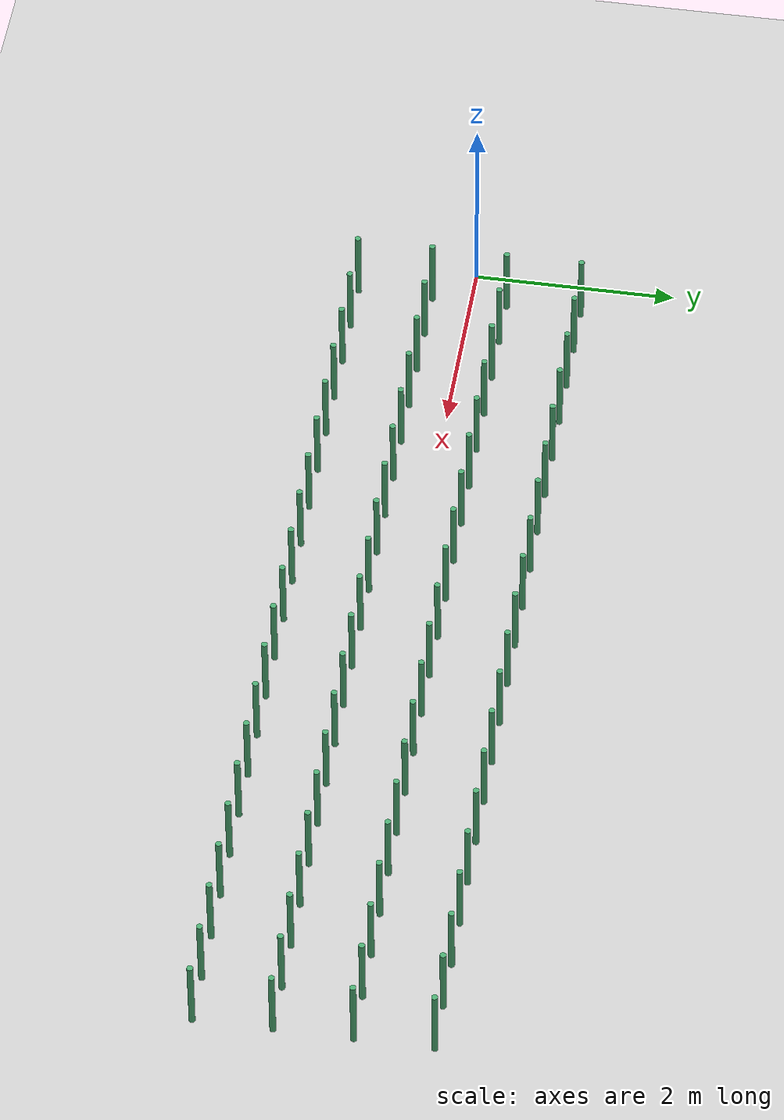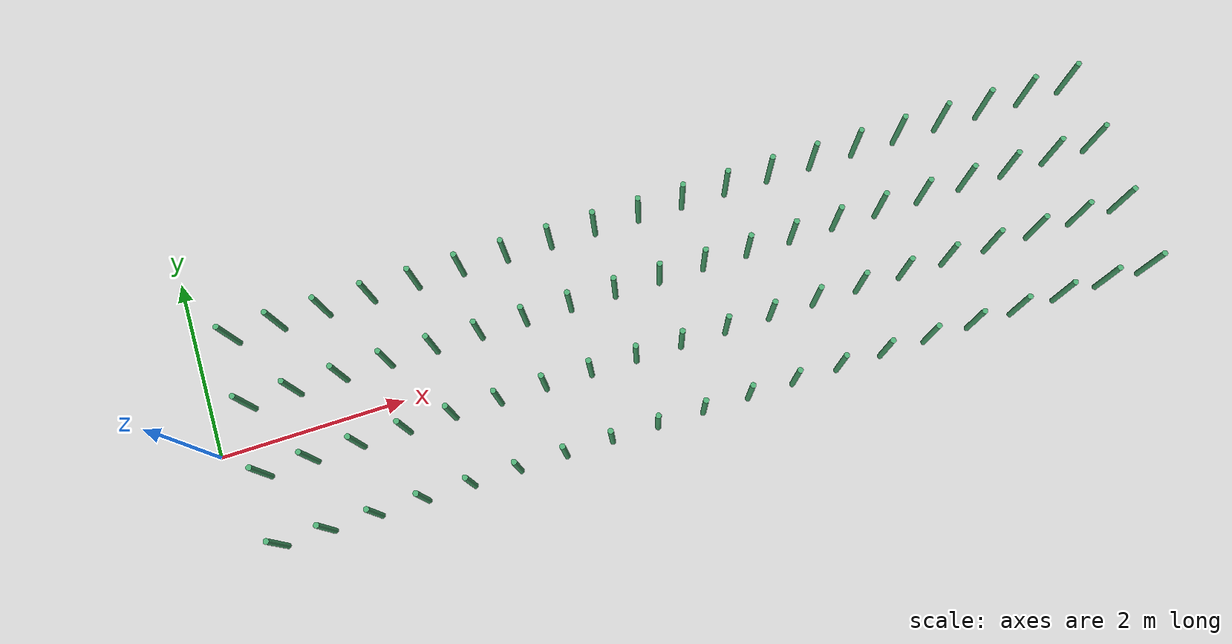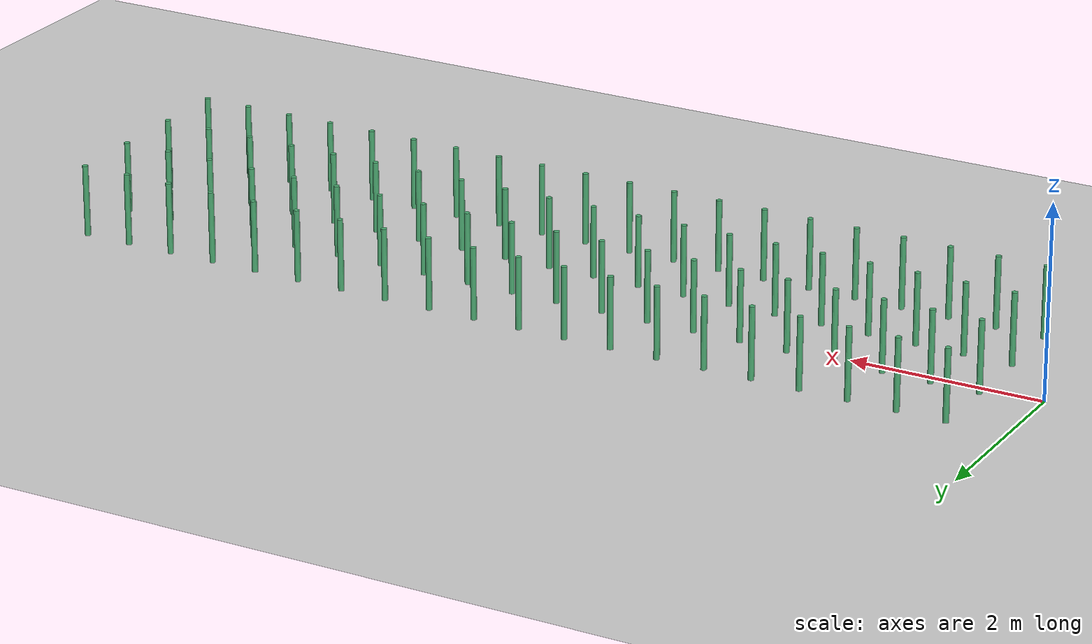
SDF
<sdf version="1.6">
 <world name="default">
  <light name="sun" type="directional">
   <pose>0 0 10 0 -0 0</pose>
   <diffuse>0.8 0.8 0.8 1</diffuse>
   <specular>0.2 0.2 0.2 1</specular>
   <attenuation>
    <range>1000</range>
    <constant>0.9</constant>
    <linear>0.01</linear>
    <quadratic>0.001</quadratic>
   </attenuation>
   <direction>-0.5 0.1 -0.9</direction>
  </light>
  <model name="ground_plane">
   <static>1</static>
   <link name="link">
    <collision name="collision">
     <geometry><plane><normal>0 0 1</normal><size>100 100</size></plane></geometry>
     <surface>
      <contact><collide_bitmask>65535</collide_bitmask></contact>
      <friction><ode><mu>100</mu><mu2>50</mu2></ode></friction>
     </surface>
    </collision>
    <visual name="visual">
     <cast_shadows>0</cast_shadows>
     <geometry><plane><normal>0 0 1</normal><size>100 100</size></plane></geometry>
     <material>
      <script><uri>file://media/materials/scripts/gazebo.material</uri><name>Gazebo/Grey</name></script>
     </material>
    </visual>
   </link>
  </model>
  <gravity>0 0 -9.8</gravity>
  <magnetic_field>6e-06 2.3e-05 -4.2e-05</magnetic_field>
  <atmosphere type="adiabatic"/>
  <physics name="default_physics" default="0" type="ode">
   <max_step_size>0.001</max_step_size>
   <real_time_factor>1</real_time_factor>
   <real_time_update_rate>1000</real_time_update_rate>
  </physics>
  <scene><ambient>0.4 0.4 0.4 1</ambient><background>0.7 0.7 0.7 1</background><shadows>1</shadows></scene>
  <audio><device>default</device></audio>
  <spherical_coordinates>
   <surface_model>EARTH_WGS84</surface_model>
   <latitude_deg>0</latitude_deg>
   <longitude_deg>0</longitude_deg>
   <elevation>0</elevation>
   <heading_deg>0</heading_deg>
  </spherical_coordinates>
  <model name="cylinder_0000">
   <pose>0.5 0.375 0.5 0 -0 0</pose>
   <link name="cylinder_0000_link">
    <inertial>
     <mass>5.0</mass>
     <inertia>
      <ixx>0.23550000000000001</ixx>
      <ixy>0</ixy>
      <ixz>0</ixz>
      <iyy>0.23550000000000001</iyy>
      <iyz>0</iyz>
      <izz>0.00225</izz>
     </inertia>
    </inertial>
    <collision name="collision">
     <geometry><cylinder><radius>0.03</radius><length>0.75</length></cylinder></geometry>
    </collision>
    <visual name="visual">
     <geometry><cylinder><radius>0.03</radius><length>0.75</length></cylinder></geometry>
     <material>
      <ambient>0.437790 0.985028 0.656685 1.0</ambient>
      <diffuse>0.297093 0.668460 0.445640 1.0</diffuse>
      <specular>0.000000 0.000000 0.000000 1.0</specular>
      <emissive>0.0 0.0 0.0 0.0</emissive>
     </material>
    </visual>
   </link>
  </model>
  <model name="cylinder_0001">
   <pose>0.5 1.125 0.5 0 -0 0</pose>
   <link name="cylinder_0001_link">
    <inertial>
     <mass>5.0</mass>
     <inertia>
      <ixx>0.23550000000000001</ixx>
      <ixy>0</ixy>
      <ixz>0</ixz>
      <iyy>0.23550000000000001</iyy>
      <iyz>0</iyz>
      <izz>0.00225</izz>
     </inertia>
    </inertial>
    <collision name="collision">
     <geometry><cylinder><radius>0.03</radius><length>0.75</length></cylinder></geometry>
    </collision>
    <visual name="visual">
     <geometry><cylinder><radius>0.03</radius><length>0.75</length></cylinder></geometry>
     <material>
      <ambient>0.437790 0.985028 0.656685 1.0</ambient>
      <diffuse>0.297093 0.668460 0.445640 1.0</diffuse>
      <specular>0.000000 0.000000 0.000000 1.0</specular>
      <emissive>0.0 0.0 0.0 0.0</emissive>
     </material>
    </visual>
   </link>
  </model>
  <model name="cylinder_0002">
   <pose>0.5 -0.375 0.5 0 -0 0</pose>
   <link name="cylinder_0002_link">
    <inertial>
     <mass>5.0</mass>
     <inertia>
      <ixx>0.23550000000000001</ixx>
      <ixy>0</ixy>
      <ixz>0</ixz>
      <iyy>0.23550000000000001</iyy>
      <iyz>0</iyz>
      <izz>0.00225</izz>
     </inertia>
    </inertial>
    <collision name="collision">
     <geometry><cylinder><radius>0.03</radius><length>0.75</length></cylinder></geometry>
    </collision>
    <visual name="visual">
     <geometry><cylinder><radius>0.03</radius><length>0.75</length></cylinder></geometry>
     <material>
      <ambient>0.437790 0.985028 0.656685 1.0</ambient>
      <diffuse>0.297093 0.668460 0.445640 1.0</diffuse>
      <specular>0.000000 0.000000 0.000000 1.0</specular>
      <emissive>0.0 0.0 0.0 0.0</emissive>
     </material>
    </visual>
   </link>
  </model>
  <model name="cylinder_0003">
   <pose>0.5 -1.125 0.5 0 -0 0</pose>
   <link name="cylinder_0003_link">
    <inertial>
     <mass>5.0</mass>
     <inertia>
      <ixx>0.23550000000000001</ixx>
      <ixy>0</ixy>
      <ixz>0</ixz>
      <iyy>0.23550000000000001</iyy>
      <iyz>0</iyz>
      <izz>0.00225</izz>
     </inertia>
    </inertial>
    <collision name="collision">
     <geometry><cylinder><radius>0.03</radius><length>0.75</length></cylinder></geometry>
    </collision>
    <visual name="visual">
     <geometry><cylinder><radius>0.03</radius><length>0.75</length></cylinder></geometry>
     <material>
      <ambient>0.437790 0.985028 0.656685 1.0</ambient>
      <diffuse>0.297093 0.668460 0.445640 1.0</diffuse>
      <specular>0.000000 0.000000 0.000000 1.0</specular>
      <emissive>0.0 0.0 0.0 0.0</emissive>
     </material>
    </visual>
   </link>
  </model>
  <model name="cylinder_0004">
   <pose>1.0 0.375 0.5 0 -0 0</pose>
   <link name="cylinder_0004_link">
    <inertial>
     <mass>5.0</mass>
     <inertia>
      <ixx>0.23550000000000001</ixx>
      <ixy>0</ixy>
      <ixz>0</ixz>
      <iyy>0.23550000000000001</iyy>
      <iyz>0</iyz>
      <izz>0.00225</izz>
     </inertia>
    </inertial>
    <collision name="collision">
     <geometry><cylinder><radius>0.03</radius><length>0.75</length></cylinder></geometry>
    </collision>
    <visual name="visual">
     <geometry><cylinder><radius>0.03</radius><length>0.75</length></cylinder></geometry>
     <material>
      <ambient>0.437790 0.985028 0.656685 1.0</ambient>
      <diffuse>0.297093 0.668460 0.445640 1.0</diffuse>
      <specular>0.000000 0.000000 0.000000 1.0</specular>
      <emissive>0.0 0.0 0.0 0.0</emissive>
     </material>
    </visual>
   </link>
  </model>
  <model name="cylinder_0005">
   <pose>1.0 1.125 0.5 0 -0 0</pose>
   <link name="cylinder_0005_link">
    <inertial>
     <mass>5.0</mass>
     <inertia>
      <ixx>0.23550000000000001</ixx>
      <ixy>0</ixy>
      <ixz>0</ixz>
      <iyy>0.23550000000000001</iyy>
      <iyz>0</iyz>
      <izz>0.00225</izz>
     </inertia>
    </inertial>
    <collision name="collision">
     <geometry><cylinder><radius>0.03</radius><length>0.75</length></cylinder></geometry>
    </collision>
    <visual name="visual">
     <geometry><cylinder><radius>0.03</radius><length>0.75</length></cylinder></geometry>
     <material>
      <ambient>0.437790 0.985028 0.656685 1.0</ambient>
      <diffuse>0.297093 0.668460 0.445640 1.0</diffuse>
      <specular>0.000000 0.000000 0.000000 1.0</specular>
      <emissive>0.0 0.0 0.0 0.0</emissive>
     </material>
    </visual>
   </link>
  </model>
  <model name="cylinder_0006">
   <pose>1.0 -0.375 0.5 0 -0 0</pose>
   <link name="cylinder_0006_link">
    <inertial>
     <mass>5.0</mass>
     <inertia>
      <ixx>0.23550000000000001</ixx>
      <ixy>0</ixy>
      <ixz>0</ixz>
      <iyy>0.23550000000000001</iyy>
      <iyz>0</iyz>
      <izz>0.00225</izz>
     </inertia>
    </inertial>
    <collision name="collision">
     <geometry><cylinder><radius>0.03</radius><length>0.75</length></cylinder></geometry>
    </collision>
    <visual name="visual">
     <geometry><cylinder><radius>0.03</radius><length>0.75</length></cylinder></geometry>
     <material>
      <ambient>0.437790 0.985028 0.656685 1.0</ambient>
      <diffuse>0.297093 0.668460 0.445640 1.0</diffuse>
      <specular>0.000000 0.000000 0.000000 1.0</specular>
      <emissive>0.0 0.0 0.0 0.0</emissive>
     </material>
    </visual>
   </link>
  </model>
  <model name="cylinder_0007">
   <pose>1.0 -1.125 0.5 0 -0 0</pose>
   <link name="cylinder_0007_link">
    <inertial>
     <mass>5.0</mass>
     <inertia>
      <ixx>0.23550000000000001</ixx>
      <ixy>0</ixy>
      <ixz>0</ixz>
      <iyy>0.23550000000000001</iyy>
      <iyz>0</iyz>
      <izz>0.00225</izz>
     </inertia>
    </inertial>
    <collision name="collision">
     <geometry><cylinder><radius>0.03</radius><length>0.75</length></cylinder></geometry>
    </collision>
    <visual name="visual">
     <geometry><cylinder><radius>0.03</radius><length>0.75</length></cylinder></geometry>
     <material>
      <ambient>0.437790 0.985028 0.656685 1.0</ambient>
      <diffuse>0.297093 0.668460 0.445640 1.0</diffuse>
      <specular>0.000000 0.000000 0.000000 1.0</specular>
      <emissive>0.0 0.0 0.0 0.0</emissive>
     </material>
    </visual>
   </link>
  </model>
  <model name="cylinder_0008">
   <pose>1.5 0.375 0.5 0 -0 0</pose>
   <link name="cylinder_0008_link">
    <inertial>
     <mass>5.0</mass>
     <inertia>
      <ixx>0.23550000000000001</ixx>
      <ixy>0</ixy>
      <ixz>0</ixz>
      <iyy>0.23550000000000001</iyy>
      <iyz>0</iyz>
      <izz>0.00225</izz>
     </inertia>
    </inertial>
    <collision name="collision">
     <geometry><cylinder><radius>0.03</radius><length>0.75</length></cylinder></geometry>
    </collision>
    <visual name="visual">
     <geometry><cylinder><radius>0.03</radius><length>0.75</length></cylinder></geometry>
     <material>
      <ambient>0.437790 0.985028 0.656685 1.0</ambient>
      <diffuse>0.297093 0.668460 0.445640 1.0</diffuse>
      <specular>0.000000 0.000000 0.000000 1.0</specular>
      <emissive>0.0 0.0 0.0 0.0</emissive>
     </material>
    </visual>
   </link>
  </model>
  <model name="cylinder_0009">
   <pose>1.5 1.125 0.5 0 -0 0</pose>
   <link name="cylinder_0009_link">
    <inertial>
     <mass>5.0</mass>
     <inertia>
      <ixx>0.23550000000000001</ixx>
      <ixy>0</ixy>
      <ixz>0</ixz>
      <iyy>0.23550000000000001</iyy>
      <iyz>0</iyz>
      <izz>0.00225</izz>
     </inertia>
    </inertial>
    <collision name="collision">
     <geometry><cylinder><radius>0.03</radius><length>0.75</length></cylinder></geometry>
    </collision>
    <visual name="visual">
     <geometry><cylinder><radius>0.03</radius><length>0.75</length></cylinder></geometry>
     <material>
      <ambient>0.437790 0.985028 0.656685 1.0</ambient>
      <diffuse>0.297093 0.668460 0.445640 1.0</diffuse>
      <specular>0.000000 0.000000 0.000000 1.0</specular>
      <emissive>0.0 0.0 0.0 0.0</emissive>
     </material>
    </visual>
   </link>
  </model>
  <model name="cylinder_0010">
   <pose>1.5 -0.375 0.5 0 -0 0</pose>
   <link name="cylinder_0010_link">
    <inertial>
     <mass>5.0</mass>
     <inertia>
      <ixx>0.23550000000000001</ixx>
      <ixy>0</ixy>
      <ixz>0</ixz>
      <iyy>0.23550000000000001</iyy>
      <iyz>0</iyz>
      <izz>0.00225</izz>
     </inertia>
    </inertial>
    <collision name="collision">
     <geometry><cylinder><radius>0.03</radius><length>0.75</length></cylinder></geometry>
    </collision>
    <visual name="visual">
     <geometry><cylinder><radius>0.03</radius><length>0.75</length></cylinder></geometry>
     <material>
      <ambient>0.437790 0.985028 0.656685 1.0</ambient>
      <diffuse>0.297093 0.668460 0.445640 1.0</diffuse>
      <specular>0.000000 0.000000 0.000000 1.0</specular>
      <emissive>0.0 0.0 0.0 0.0</emissive>
     </material>
    </visual>
   </link>
  </model>
  <model name="cylinder_0011">
   <pose>1.5 -1.125 0.5 0 -0 0</pose>
   <link name="cylinder_0011_link">
    <inertial>
     <mass>5.0</mass>
     <inertia>
      <ixx>0.23550000000000001</ixx>
      <ixy>0</ixy>
      <ixz>0</ixz>
      <iyy>0.23550000000000001</iyy>
      <iyz>0</iyz>
      <izz>0.00225</izz>
     </inertia>
    </inertial>
    <collision name="collision">
     <geometry><cylinder><radius>0.03</radius><length>0.75</length></cylinder></geometry>
    </collision>
    <visual name="visual">
     <geometry><cylinder><radius>0.03</radius><length>0.75</length></cylinder></geometry>
     <material>
      <ambient>0.437790 0.985028 0.656685 1.0</ambient>
      <diffuse>0.297093 0.668460 0.445640 1.0</diffuse>
      <specular>0.000000 0.000000 0.000000 1.0</specular>
      <emissive>0.0 0.0 0.0 0.0</emissive>
     </material>
    </visual>
   </link>
  </model>
  <model name="cylinder_0012">
   <pose>2.0 0.375 0.5 0 -0 0</pose>
   <link name="cylinder_0012_link">
    <inertial>
     <mass>5.0</mass>
     <inertia>
      <ixx>0.23550000000000001</ixx>
      <ixy>0</ixy>
      <ixz>0</ixz>
      <iyy>0.23550000000000001</iyy>
      <iyz>0</iyz>
      <izz>0.00225</izz>
     </inertia>
    </inertial>
    <collision name="collision">
     <geometry><cylinder><radius>0.03</radius><length>0.75</length></cylinder></geometry>
    </collision>
    <visual name="visual">
     <geometry><cylinder><radius>0.03</radius><length>0.75</length></cylinder></geometry>
     <material>
      <ambient>0.437790 0.985028 0.656685 1.0</ambient>
      <diffuse>0.297093 0.668460 0.445640 1.0</diffuse>
      <specular>0.000000 0.000000 0.000000 1.0</specular>
      <emissive>0.0 0.0 0.0 0.0</emissive>
     </material>
    </visual>
   </link>
  </model>
  <model name="cylinder_0013">
   <pose>2.0 1.125 0.5 0 -0 0</pose>
   <link name="cylinder_0013_link">
    <inertial>
     <mass>5.0</mass>
     <inertia>
      <ixx>0.23550000000000001</ixx>
      <ixy>0</ixy>
      <ixz>0</ixz>
      <iyy>0.23550000000000001</iyy>
      <iyz>0</iyz>
      <izz>0.00225</izz>
     </inertia>
    </inertial>
    <collision name="collision">
     <geometry><cylinder><radius>0.03</radius><length>0.75</length></cylinder></geometry>
    </collision>
    <visual name="visual">
     <geometry><cylinder><radius>0.03</radius><length>0.75</length></cylinder></geometry>
     <material>
      <ambient>0.437790 0.985028 0.656685 1.0</ambient>
      <diffuse>0.297093 0.668460 0.445640 1.0</diffuse>
      <specular>0.000000 0.000000 0.000000 1.0</specular>
      <emissive>0.0 0.0 0.0 0.0</emissive>
     </material>
    </visual>
   </link>
  </model>
  <model name="cylinder_0014">
   <pose>2.0 -0.375 0.5 0 -0 0</pose>
   <link name="cylinder_0014_link">
    <inertial>
     <mass>5.0</mass>
     <inertia>
      <ixx>0.23550000000000001</ixx>
      <ixy>0</ixy>
      <ixz>0</ixz>
      <iyy>0.23550000000000001</iyy>
      <iyz>0</iyz>
      <izz>0.00225</izz>
     </inertia>
    </inertial>
    <collision name="collision">
     <geometry><cylinder><radius>0.03</radius><length>0.75</length></cylinder></geometry>
    </collision>
    <visual name="visual">
     <geometry><cylinder><radius>0.03</radius><length>0.75</length></cylinder></geometry>
     <material>
      <ambient>0.437790 0.985028 0.656685 1.0</ambient>
      <diffuse>0.297093 0.668460 0.445640 1.0</diffuse>
      <specular>0.000000 0.000000 0.000000 1.0</specular>
      <emissive>0.0 0.0 0.0 0.0</emissive>
     </material>
    </visual>
   </link>
  </model>
  <model name="cylinder_0015">
   <pose>2.0 -1.125 0.5 0 -0 0</pose>
   <link name="cylinder_0015_link">
    <inertial>
     <mass>5.0</mass>
     <inertia>
      <ixx>0.23550000000000001</ixx>
      <ixy>0</ixy>
      <ixz>0</ixz>
      <iyy>0.23550000000000001</iyy>
      <iyz>0</iyz>
      <izz>0.00225</izz>
     </inertia>
    </inertial>
    <collision name="collision">
     <geometry><cylinder><radius>0.03</radius><length>0.75</length></cylinder></geometry>
    </collision>
    <visual name="visual">
     <geometry><cylinder><radius>0.03</radius><length>0.75</length></cylinder></geometry>
     <material>
      <ambient>0.437790 0.985028 0.656685 1.0</ambient>
      <diffuse>0.297093 0.668460 0.445640 1.0</diffuse>
      <specular>0.000000 0.000000 0.000000 1.0</specular>
      <emissive>0.0 0.0 0.0 0.0</emissive>
     </material>
    </visual>
   </link>
  </model>
  <model name="cylinder_0016">
   <pose>2.5 0.375 0.5 0 -0 0</pose>
   <link name="cylinder_0016_link">
    <inertial>
     <mass>5.0</mass>
     <inertia>
      <ixx>0.23550000000000001</ixx>
      <ixy>0</ixy>
      <ixz>0</ixz>
      <iyy>0.23550000000000001</iyy>
      <iyz>0</iyz>
      <izz>0.00225</izz>
     </inertia>
    </inertial>
    <collision name="collision">
     <geometry><cylinder><radius>0.03</radius><length>0.75</length></cylinder></geometry>
    </collision>
    <visual name="visual">
     <geometry><cylinder><radius>0.03</radius><length>0.75</length></cylinder></geometry>
     <material>
      <ambient>0.437790 0.985028 0.656685 1.0</ambient>
      <diffuse>0.297093 0.668460 0.445640 1.0</diffuse>
      <specular>0.000000 0.000000 0.000000 1.0</specular>
      <emissive>0.0 0.0 0.0 0.0</emissive>
     </material>
    </visual>
   </link>
  </model>
  <model name="cylinder_0017">
   <pose>2.5 1.125 0.5 0 -0 0</pose>
   <link name="cylinder_0017_link">
    <inertial>
     <mass>5.0</mass>
     <inertia>
      <ixx>0.23550000000000001</ixx>
      <ixy>0</ixy>
      <ixz>0</ixz>
      <iyy>0.23550000000000001</iyy>
      <iyz>0</iyz>
      <izz>0.00225</izz>
     </inertia>
    </inertial>
    <collision name="collision">
     <geometry><cylinder><radius>0.03</radius><length>0.75</length></cylinder></geometry>
    </collision>
    <visual name="visual">
     <geometry><cylinder><radius>0.03</radius><length>0.75</length></cylinder></geometry>
     <material>
      <ambient>0.437790 0.985028 0.656685 1.0</ambient>
      <diffuse>0.297093 0.668460 0.445640 1.0</diffuse>
      <specular>0.000000 0.000000 0.000000 1.0</specular>
      <emissive>0.0 0.0 0.0 0.0</emissive>
     </material>
    </visual>
   </link>
  </model>
  <model name="cylinder_0018">
   <pose>2.5 -0.375 0.5 0 -0 0</pose>
   <link name="cylinder_0018_link">
    <inertial>
     <mass>5.0</mass>
     <inertia>
      <ixx>0.23550000000000001</ixx>
      <ixy>0</ixy>
      <ixz>0</ixz>
      <iyy>0.23550000000000001</iyy>
      <iyz>0</iyz>
      <izz>0.00225</izz>
     </inertia>
    </inertial>
    <collision name="collision">
     <geometry><cylinder><radius>0.03</radius><length>0.75</length></cylinder></geometry>
    </collision>
    <visual name="visual">
     <geometry><cylinder><radius>0.03</radius><length>0.75</length></cylinder></geometry>
     <material>
      <ambient>0.437790 0.985028 0.656685 1.0</ambient>
      <diffuse>0.297093 0.668460 0.445640 1.0</diffuse>
      <specular>0.000000 0.000000 0.000000 1.0</specular>
      <emissive>0.0 0.0 0.0 0.0</emissive>
     </material>
    </visual>
   </link>
  </model>
  <model name="cylinder_0019">
   <pose>2.5 -1.125 0.5 0 -0 0</pose>
   <link name="cylinder_0019_link">
    <inertial>
     <mass>5.0</mass>
     <inertia>
      <ixx>0.23550000000000001</ixx>
      <ixy>0</ixy>
      <ixz>0</ixz>
      <iyy>0.23550000000000001</iyy>
      <iyz>0</iyz>
      <izz>0.00225</izz>
     </inertia>
    </inertial>
    <collision name="collision">
     <geometry><cylinder><radius>0.03</radius><length>0.75</length></cylinder></geometry>
    </collision>
    <visual name="visual">
     <geometry><cylinder><radius>0.03</radius><length>0.75</length></cylinder></geometry>
     <material>
      <ambient>0.437790 0.985028 0.656685 1.0</ambient>
      <diffuse>0.297093 0.668460 0.445640 1.0</diffuse>
      <specular>0.000000 0.000000 0.000000 1.0</specular>
      <emissive>0.0 0.0 0.0 0.0</emissive>
     </material>
    </visual>
   </link>
  </model>
  <model name="cylinder_0020">
   <pose>3.0 0.375 0.5 0 -0 0</pose>
   <link name="cylinder_0020_link">
    <inertial>
     <mass>5.0</mass>
     <inertia>
      <ixx>0.23550000000000001</ixx>
      <ixy>0</ixy>
      <ixz>0</ixz>
      <iyy>0.23550000000000001</iyy>
      <iyz>0</iyz>
      <izz>0.00225</izz>
     </inertia>
    </inertial>
    <collision name="collision">
     <geometry><cylinder><radius>0.03</radius><length>0.75</length></cylinder></geometry>
    </collision>
    <visual name="visual">
     <geometry><cylinder><radius>0.03</radius><length>0.75</length></cylinder></geometry>
     <material>
      <ambient>0.437790 0.985028 0.656685 1.0</ambient>
      <diffuse>0.297093 0.668460 0.445640 1.0</diffuse>
      <specular>0.000000 0.000000 0.000000 1.0</specular>
      <emissive>0.0 0.0 0.0 0.0</emissive>
     </material>
    </visual>
   </link>
  </model>
  <model name="cylinder_0021">
   <pose>3.0 1.125 0.5 0 -0 0</pose>
   <link name="cylinder_0021_link">
    <inertial>
     <mass>5.0</mass>
     <inertia>
      <ixx>0.23550000000000001</ixx>
      <ixy>0</ixy>
      <ixz>0</ixz>
      <iyy>0.23550000000000001</iyy>
      <iyz>0</iyz>
      <izz>0.00225</izz>
     </inertia>
    </inertial>
    <collision name="collision">
     <geometry><cylinder><radius>0.03</radius><length>0.75</length></cylinder></geometry>
    </collision>
    <visual name="visual">
     <geometry><cylinder><radius>0.03</radius><length>0.75</length></cylinder></geometry>
     <material>
      <ambient>0.437790 0.985028 0.656685 1.0</ambient>
      <diffuse>0.297093 0.668460 0.445640 1.0</diffuse>
      <specular>0.000000 0.000000 0.000000 1.0</specular>
      <emissive>0.0 0.0 0.0 0.0</emissive>
     </material>
    </visual>
   </link>
  </model>
  <model name="cylinder_0022">
   <pose>3.0 -0.375 0.5 0 -0 0</pose>
   <link name="cylinder_0022_link">
    <inertial>
     <mass>5.0</mass>
     <inertia>
      <ixx>0.23550000000000001</ixx>
      <ixy>0</ixy>
      <ixz>0</ixz>
      <iyy>0.23550000000000001</iyy>
      <iyz>0</iyz>
      <izz>0.00225</izz>
     </inertia>
    </inertial>
    <collision name="collision">
     <geometry><cylinder><radius>0.03</radius><length>0.75</length></cylinder></geometry>
    </collision>
    <visual name="visual">
     <geometry><cylinder><radius>0.03</radius><length>0.75</length></cylinder></geometry>
     <material>
      <ambient>0.437790 0.985028 0.656685 1.0</ambient>
      <diffuse>0.297093 0.668460 0.445640 1.0</diffuse>
      <specular>0.000000 0.000000 0.000000 1.0</specular>
      <emissive>0.0 0.0 0.0 0.0</emissive>
     </material>
    </visual>
   </link>
  </model>
  <model name="cylinder_0023">
   <pose>3.0 -1.125 0.5 0 -0 0</pose>
   <link name="cylinder_0023_link">
    <inertial>
     <mass>5.0</mass>
     <inertia>
      <ixx>0.23550000000000001</ixx>
      <ixy>0</ixy>
      <ixz>0</ixz>
      <iyy>0.23550000000000001</iyy>
      <iyz>0</iyz>
      <izz>0.00225</izz>
     </inertia>
    </inertial>
    <collision name="collision">
     <geometry><cylinder><radius>0.03</radius><length>0.75</length></cylinder></geometry>
    </collision>
    <visual name="visual">
     <geometry><cylinder><radius>0.03</radius><length>0.75</length></cylinder></geometry>
     <material>
      <ambient>0.437790 0.985028 0.656685 1.0</ambient>
      <diffuse>0.297093 0.668460 0.445640 1.0</diffuse>
      <specular>0.000000 0.000000 0.000000 1.0</specular>
      <emissive>0.0 0.0 0.0 0.0</emissive>
     </material>
    </visual>
   </link>
  </model>
  <model name="cylinder_0024">
   <pose>3.5 0.375 0.5 0 -0 0</pose>
   <link name="cylinder_0024_link">
    <inertial>
     <mass>5.0</mass>
     <inertia>
      <ixx>0.23550000000000001</ixx>
      <ixy>0</ixy>
      <ixz>0</ixz>
      <iyy>0.23550000000000001</iyy>
      <iyz>0</iyz>
      <izz>0.00225</izz>
     </inertia>
    </inertial>
    <collision name="collision">
     <geometry><cylinder><radius>0.03</radius><length>0.75</length></cylinder></geometry>
    </collision>
    <visual name="visual">
     <geometry><cylinder><radius>0.03</radius><length>0.75</length></cylinder></geometry>
     <material>
      <ambient>0.437790 0.985028 0.656685 1.0</ambient>
      <diffuse>0.297093 0.668460 0.445640 1.0</diffuse>
      <specular>0.000000 0.000000 0.000000 1.0</specular>
      <emissive>0.0 0.0 0.0 0.0</emissive>
     </material>
    </visual>
   </link>
  </model>
  <model name="cylinder_0025">
   <pose>3.5 1.125 0.5 0 -0 0</pose>
   <link name="cylinder_0025_link">
    <inertial>
     <mass>5.0</mass>
     <inertia>
      <ixx>0.23550000000000001</ixx>
      <ixy>0</ixy>
      <ixz>0</ixz>
      <iyy>0.23550000000000001</iyy>
      <iyz>0</iyz>
      <izz>0.00225</izz>
     </inertia>
    </inertial>
    <collision name="collision">
     <geometry><cylinder><radius>0.03</radius><length>0.75</length></cylinder></geometry>
    </collision>
    <visual name="visual">
     <geometry><cylinder><radius>0.03</radius><length>0.75</length></cylinder></geometry>
     <material>
      <ambient>0.437790 0.985028 0.656685 1.0</ambient>
      <diffuse>0.297093 0.668460 0.445640 1.0</diffuse>
      <specular>0.000000 0.000000 0.000000 1.0</specular>
      <emissive>0.0 0.0 0.0 0.0</emissive>
     </material>
    </visual>
   </link>
  </model>
  <model name="cylinder_0026">
   <pose>3.5 -0.375 0.5 0 -0 0</pose>
   <link name="cylinder_0026_link">
    <inertial>
     <mass>5.0</mass>
     <inertia>
      <ixx>0.23550000000000001</ixx>
      <ixy>0</ixy>
      <ixz>0</ixz>
      <iyy>0.23550000000000001</iyy>
      <iyz>0</iyz>
      <izz>0.00225</izz>
     </inertia>
    </inertial>
    <collision name="collision">
     <geometry><cylinder><radius>0.03</radius><length>0.75</length></cylinder></geometry>
    </collision>
    <visual name="visual">
     <geometry><cylinder><radius>0.03</radius><length>0.75</length></cylinder></geometry>
     <material>
      <ambient>0.437790 0.985028 0.656685 1.0</ambient>
      <diffuse>0.297093 0.668460 0.445640 1.0</diffuse>
      <specular>0.000000 0.000000 0.000000 1.0</specular>
      <emissive>0.0 0.0 0.0 0.0</emissive>
     </material>
    </visual>
   </link>
  </model>
  <model name="cylinder_0027">
   <pose>3.5 -1.125 0.5 0 -0 0</pose>
   <link name="cylinder_0027_link">
    <inertial>
     <mass>5.0</mass>
     <inertia>
      <ixx>0.23550000000000001</ixx>
      <ixy>0</ixy>
      <ixz>0</ixz>
      <iyy>0.23550000000000001</iyy>
      <iyz>0</iyz>
      <izz>0.00225</izz>
     </inertia>
    </inertial>
    <collision name="collision">
     <geometry><cylinder><radius>0.03</radius><length>0.75</length></cylinder></geometry>
    </collision>
    <visual name="visual">
     <geometry><cylinder><radius>0.03</radius><length>0.75</length></cylinder></geometry>
     <material>
      <ambient>0.437790 0.985028 0.656685 1.0</ambient>
      <diffuse>0.297093 0.668460 0.445640 1.0</diffuse>
      <specular>0.000000 0.000000 0.000000 1.0</specular>
      <emissive>0.0 0.0 0.0 0.0</emissive>
     </material>
    </visual>
   </link>
  </model>
  <model name="cylinder_0028">
   <pose>4.0 0.375 0.5 0 -0 0</pose>
   <link name="cylinder_0028_link">
    <inertial>
     <mass>5.0</mass>
     <inertia>
      <ixx>0.23550000000000001</ixx>
      <ixy>0</ixy>
      <ixz>0</ixz>
      <iyy>0.23550000000000001</iyy>
      <iyz>0</iyz>
      <izz>0.00225</izz>
     </inertia>
    </inertial>
    <collision name="collision">
     <geometry><cylinder><radius>0.03</radius><length>0.75</length></cylinder></geometry>
    </collision>
    <visual name="visual">
     <geometry><cylinder><radius>0.03</radius><length>0.75</length></cylinder></geometry>
     <material>
      <ambient>0.437790 0.985028 0.656685 1.0</ambient>
      <diffuse>0.297093 0.668460 0.445640 1.0</diffuse>
      <specular>0.000000 0.000000 0.000000 1.0</specular>
      <emissive>0.0 0.0 0.0 0.0</emissive>
     </material>
    </visual>
   </link>
  </model>
  <model name="cylinder_0029">
   <pose>4.0 1.125 0.5 0 -0 0</pose>
   <link name="cylinder_0029_link">
    <inertial>
     <mass>5.0</mass>
     <inertia>
      <ixx>0.23550000000000001</ixx>
      <ixy>0</ixy>
      <ixz>0</ixz>
      <iyy>0.23550000000000001</iyy>
      <iyz>0</iyz>
      <izz>0.00225</izz>
     </inertia>
    </inertial>
    <collision name="collision">
     <geometry><cylinder><radius>0.03</radius><length>0.75</length></cylinder></geometry>
    </collision>
    <visual name="visual">
     <geometry><cylinder><radius>0.03</radius><length>0.75</length></cylinder></geometry>
     <material>
      <ambient>0.437790 0.985028 0.656685 1.0</ambient>
      <diffuse>0.297093 0.668460 0.445640 1.0</diffuse>
      <specular>0.000000 0.000000 0.000000 1.0</specular>
      <emissive>0.0 0.0 0.0 0.0</emissive>
     </material>
    </visual>
   </link>
  </model>
  <model name="cylinder_0030">
   <pose>4.0 -0.375 0.5 0 -0 0</pose>
   <link name="cylinder_0030_link">
    <inertial>
     <mass>5.0</mass>
     <inertia>
      <ixx>0.23550000000000001</ixx>
      <ixy>0</ixy>
      <ixz>0</ixz>
      <iyy>0.23550000000000001</iyy>
      <iyz>0</iyz>
      <izz>0.00225</izz>
     </inertia>
    </inertial>
    <collision name="collision">
     <geometry><cylinder><radius>0.03</radius><length>0.75</length></cylinder></geometry>
    </collision>
    <visual name="visual">
     <geometry><cylinder><radius>0.03</radius><length>0.75</length></cylinder></geometry>
     <material>
      <ambient>0.437790 0.985028 0.656685 1.0</ambient>
      <diffuse>0.297093 0.668460 0.445640 1.0</diffuse>
      <specular>0.000000 0.000000 0.000000 1.0</specular>
      <emissive>0.0 0.0 0.0 0.0</emissive>
     </material>
    </visual>
   </link>
  </model>
  <model name="cylinder_0031">
   <pose>4.0 -1.125 0.5 0 -0 0</pose>
   <link name="cylinder_0031_link">
    <inertial>
     <mass>5.0</mass>
     <inertia>
      <ixx>0.23550000000000001</ixx>
      <ixy>0</ixy>
      <ixz>0</ixz>
      <iyy>0.23550000000000001</iyy>
      <iyz>0</iyz>
      <izz>0.00225</izz>
     </inertia>
    </inertial>
    <collision name="collision">
     <geometry><cylinder><radius>0.03</radius><length>0.75</length></cylinder></geometry>
    </collision>
    <visual name="visual">
     <geometry><cylinder><radius>0.03</radius><length>0.75</length></cylinder></geometry>
     <material>
      <ambient>0.437790 0.985028 0.656685 1.0</ambient>
      <diffuse>0.297093 0.668460 0.445640 1.0</diffuse>
      <specular>0.000000 0.000000 0.000000 1.0</specular>
      <emissive>0.0 0.0 0.0 0.0</emissive>
     </material>
    </visual>
   </link>
  </model>
  <model name="cylinder_0032">
   <pose>4.5 0.375 0.5 0 -0 0</pose>
   <link name="cylinder_0032_link">
    <inertial>
     <mass>5.0</mass>
     <inertia>
      <ixx>0.23550000000000001</ixx>
      <ixy>0</ixy>
      <ixz>0</ixz>
      <iyy>0.23550000000000001</iyy>
      <iyz>0</iyz>
      <izz>0.00225</izz>
     </inertia>
    </inertial>
    <collision name="collision">
     <geometry><cylinder><radius>0.03</radius><length>0.75</length></cylinder></geometry>
    </collision>
    <visual name="visual">
     <geometry><cylinder><radius>0.03</radius><length>0.75</length></cylinder></geometry>
     <material>
      <ambient>0.437790 0.985028 0.656685 1.0</ambient>
      <diffuse>0.297093 0.668460 0.445640 1.0</diffuse>
      <specular>0.000000 0.000000 0.000000 1.0</specular>
      <emissive>0.0 0.0 0.0 0.0</emissive>
     </material>
    </visual>
   </link>
  </model>
  <model name="cylinder_0033">
   <pose>4.5 1.125 0.5 0 -0 0</pose>
   <link name="cylinder_0033_link">
    <inertial>
     <mass>5.0</mass>
     <inertia>
      <ixx>0.23550000000000001</ixx>
      <ixy>0</ixy>
      <ixz>0</ixz>
      <iyy>0.23550000000000001</iyy>
      <iyz>0</iyz>
      <izz>0.00225</izz>
     </inertia>
    </inertial>
    <collision name="collision">
     <geometry><cylinder><radius>0.03</radius><length>0.75</length></cylinder></geometry>
    </collision>
    <visual name="visual">
     <geometry><cylinder><radius>0.03</radius><length>0.75</length></cylinder></geometry>
     <material>
      <ambient>0.437790 0.985028 0.656685 1.0</ambient>
      <diffuse>0.297093 0.668460 0.445640 1.0</diffuse>
      <specular>0.000000 0.000000 0.000000 1.0</specular>
      <emissive>0.0 0.0 0.0 0.0</emissive>
     </material>
    </visual>
   </link>
  </model>
  <model name="cylinder_0034">
   <pose>4.5 -0.375 0.5 0 -0 0</pose>
   <link name="cylinder_0034_link">
    <inertial>
     <mass>5.0</mass>
     <inertia>
      <ixx>0.23550000000000001</ixx>
      <ixy>0</ixy>
      <ixz>0</ixz>
      <iyy>0.23550000000000001</iyy>
      <iyz>0</iyz>
      <izz>0.00225</izz>
     </inertia>
    </inertial>
    <collision name="collision">
     <geometry><cylinder><radius>0.03</radius><length>0.75</length></cylinder></geometry>
    </collision>
    <visual name="visual">
     <geometry><cylinder><radius>0.03</radius><length>0.75</length></cylinder></geometry>
     <material>
      <ambient>0.437790 0.985028 0.656685 1.0</ambient>
      <diffuse>0.297093 0.668460 0.445640 1.0</diffuse>
      <specular>0.000000 0.000000 0.000000 1.0</specular>
      <emissive>0.0 0.0 0.0 0.0</emissive>
     </material>
    </visual>
   </link>
  </model>
  <model name="cylinder_0035">
   <pose>4.5 -1.125 0.5 0 -0 0</pose>
   <link name="cylinder_0035_link">
    <inertial>
     <mass>5.0</mass>
     <inertia>
      <ixx>0.23550000000000001</ixx>
      <ixy>0</ixy>
      <ixz>0</ixz>
      <iyy>0.23550000000000001</iyy>
      <iyz>0</iyz>
      <izz>0.00225</izz>
     </inertia>
    </inertial>
    <collision name="collision">
     <geometry><cylinder><radius>0.03</radius><length>0.75</length></cylinder></geometry>
    </collision>
    <visual name="visual">
     <geometry><cylinder><radius>0.03</radius><length>0.75</length></cylinder></geometry>
     <material>
      <ambient>0.437790 0.985028 0.656685 1.0</ambient>
      <diffuse>0.297093 0.668460 0.445640 1.0</diffuse>
      <specular>0.000000 0.000000 0.000000 1.0</specular>
      <emissive>0.0 0.0 0.0 0.0</emissive>
     </material>
    </visual>
   </link>
  </model>
  <model name="cylinder_0036">
   <pose>5.0 0.375 0.5 0 -0 0</pose>
   <link name="cylinder_0036_link">
    <inertial>
     <mass>5.0</mass>
     <inertia>
      <ixx>0.23550000000000001</ixx>
      <ixy>0</ixy>
      <ixz>0</ixz>
      <iyy>0.23550000000000001</iyy>
      <iyz>0</iyz>
      <izz>0.00225</izz>
     </inertia>
    </inertial>
    <collision name="collision">
     <geometry><cylinder><radius>0.03</radius><length>0.75</length></cylinder></geometry>
    </collision>
    <visual name="visual">
     <geometry><cylinder><radius>0.03</radius><length>0.75</length></cylinder></geometry>
     <material>
      <ambient>0.437790 0.985028 0.656685 1.0</ambient>
      <diffuse>0.297093 0.668460 0.445640 1.0</diffuse>
      <specular>0.000000 0.000000 0.000000 1.0</specular>
      <emissive>0.0 0.0 0.0 0.0</emissive>
     </material>
    </visual>
   </link>
  </model>
  <model name="cylinder_0037">
   <pose>5.0 1.125 0.5 0 -0 0</pose>
   <link name="cylinder_0037_link">
    <inertial>
     <mass>5.0</mass>
     <inertia>
      <ixx>0.23550000000000001</ixx>
      <ixy>0</ixy>
      <ixz>0</ixz>
      <iyy>0.23550000000000001</iyy>
      <iyz>0</iyz>
      <izz>0.00225</izz>
     </inertia>
    </inertial>
    <collision name="collision">
     <geometry><cylinder><radius>0.03</radius><length>0.75</length></cylinder></geometry>
    </collision>
    <visual name="visual">
     <geometry><cylinder><radius>0.03</radius><length>0.75</length></cylinder></geometry>
     <material>
      <ambient>0.437790 0.985028 0.656685 1.0</ambient>
      <diffuse>0.297093 0.668460 0.445640 1.0</diffuse>
      <specular>0.000000 0.000000 0.000000 1.0</specular>
      <emissive>0.0 0.0 0.0 0.0</emissive>
     </material>
    </visual>
   </link>
  </model>
  <model name="cylinder_0038">
   <pose>5.0 -0.375 0.5 0 -0 0</pose>
   <link name="cylinder_0038_link">
    <inertial>
     <mass>5.0</mass>
     <inertia>
      <ixx>0.23550000000000001</ixx>
      <ixy>0</ixy>
      <ixz>0</ixz>
      <iyy>0.23550000000000001</iyy>
      <iyz>0</iyz>
      <izz>0.00225</izz>
     </inertia>
    </inertial>
    <collision name="collision">
     <geometry><cylinder><radius>0.03</radius><length>0.75</length></cylinder></geometry>
    </collision>
    <visual name="visual">
     <geometry><cylinder><radius>0.03</radius><length>0.75</length></cylinder></geometry>
     <material>
      <ambient>0.437790 0.985028 0.656685 1.0</ambient>
      <diffuse>0.297093 0.668460 0.445640 1.0</diffuse>
      <specular>0.000000 0.000000 0.000000 1.0</specular>
      <emissive>0.0 0.0 0.0 0.0</emissive>
     </material>
    </visual>
   </link>
  </model>
  <model name="cylinder_0039">
   <pose>5.0 -1.125 0.5 0 -0 0</pose>
   <link name="cylinder_0039_link">
    <inertial>
     <mass>5.0</mass>
     <inertia>
      <ixx>0.23550000000000001</ixx>
      <ixy>0</ixy>
      <ixz>0</ixz>
      <iyy>0.23550000000000001</iyy>
      <iyz>0</iyz>
      <izz>0.00225</izz>
     </inertia>
    </inertial>
    <collision name="collision">
     <geometry><cylinder><radius>0.03</radius><length>0.75</length></cylinder></geometry>
    </collision>
    <visual name="visual">
     <geometry><cylinder><radius>0.03</radius><length>0.75</length></cylinder></geometry>
     <material>
      <ambient>0.437790 0.985028 0.656685 1.0</ambient>
      <diffuse>0.297093 0.668460 0.445640 1.0</diffuse>
      <specular>0.000000 0.000000 0.000000 1.0</specular>
      <emissive>0.0 0.0 0.0 0.0</emissive>
     </material>
    </visual>
   </link>
  </model>
  <model name="cylinder_0040">
   <pose>5.5 0.375 0.5 0 -0 0</pose>
   <link name="cylinder_0040_link">
    <inertial>
     <mass>5.0</mass>
     <inertia>
      <ixx>0.23550000000000001</ixx>
      <ixy>0</ixy>
      <ixz>0</ixz>
      <iyy>0.23550000000000001</iyy>
      <iyz>0</iyz>
      <izz>0.00225</izz>
     </inertia>
    </inertial>
    <collision name="collision">
     <geometry><cylinder><radius>0.03</radius><length>0.75</length></cylinder></geometry>
    </collision>
    <visual name="visual">
     <geometry><cylinder><radius>0.03</radius><length>0.75</length></cylinder></geometry>
     <material>
      <ambient>0.437790 0.985028 0.656685 1.0</ambient>
      <diffuse>0.297093 0.668460 0.445640 1.0</diffuse>
      <specular>0.000000 0.000000 0.000000 1.0</specular>
      <emissive>0.0 0.0 0.0 0.0</emissive>
     </material>
    </visual>
   </link>
  </model>
  <model name="cylinder_0041">
   <pose>5.5 1.125 0.5 0 -0 0</pose>
   <link name="cylinder_0041_link">
    <inertial>
     <mass>5.0</mass>
     <inertia>
      <ixx>0.23550000000000001</ixx>
      <ixy>0</ixy>
      <ixz>0</ixz>
      <iyy>0.23550000000000001</iyy>
      <iyz>0</iyz>
      <izz>0.00225</izz>
     </inertia>
    </inertial>
    <collision name="collision">
     <geometry><cylinder><radius>0.03</radius><length>0.75</length></cylinder></geometry>
    </collision>
    <visual name="visual">
     <geometry><cylinder><radius>0.03</radius><length>0.75</length></cylinder></geometry>
     <material>
      <ambient>0.437790 0.985028 0.656685 1.0</ambient>
      <diffuse>0.297093 0.668460 0.445640 1.0</diffuse>
      <specular>0.000000 0.000000 0.000000 1.0</specular>
      <emissive>0.0 0.0 0.0 0.0</emissive>
     </material>
    </visual>
   </link>
  </model>
  <model name="cylinder_0042">
   <pose>5.5 -0.375 0.5 0 -0 0</pose>
   <link name="cylinder_0042_link">
    <inertial>
     <mass>5.0</mass>
     <inertia>
      <ixx>0.23550000000000001</ixx>
      <ixy>0</ixy>
      <ixz>0</ixz>
      <iyy>0.23550000000000001</iyy>
      <iyz>0</iyz>
      <izz>0.00225</izz>
     </inertia>
    </inertial>
    <collision name="collision">
     <geometry><cylinder><radius>0.03</radius><length>0.75</length></cylinder></geometry>
    </collision>
    <visual name="visual">
     <geometry><cylinder><radius>0.03</radius><length>0.75</length></cylinder></geometry>
     <material>
      <ambient>0.437790 0.985028 0.656685 1.0</ambient>
      <diffuse>0.297093 0.668460 0.445640 1.0</diffuse>
      <specular>0.000000 0.000000 0.000000 1.0</specular>
      <emissive>0.0 0.0 0.0 0.0</emissive>
     </material>
    </visual>
   </link>
  </model>
  <model name="cylinder_0043">
   <pose>5.5 -1.125 0.5 0 -0 0</pose>
   <link name="cylinder_0043_link">
    <inertial>
     <mass>5.0</mass>
     <inertia>
      <ixx>0.23550000000000001</ixx>
      <ixy>0</ixy>
      <ixz>0</ixz>
      <iyy>0.23550000000000001</iyy>
      <iyz>0</iyz>
      <izz>0.00225</izz>
     </inertia>
    </inertial>
    <collision name="collision">
     <geometry><cylinder><radius>0.03</radius><length>0.75</length></cylinder></geometry>
    </collision>
    <visual name="visual">
     <geometry><cylinder><radius>0.03</radius><length>0.75</length></cylinder></geometry>
     <material>
      <ambient>0.437790 0.985028 0.656685 1.0</ambient>
      <diffuse>0.297093 0.668460 0.445640 1.0</diffuse>
      <specular>0.000000 0.000000 0.000000 1.0</specular>
      <emissive>0.0 0.0 0.0 0.0</emissive>
     </material>
    </visual>
   </link>
  </model>
  <model name="cylinder_0044">
   <pose>6.0 0.375 0.5 0 -0 0</pose>
   <link name="cylinder_0044_link">
    <inertial>
     <mass>5.0</mass>
     <inertia>
      <ixx>0.23550000000000001</ixx>
      <ixy>0</ixy>
      <ixz>0</ixz>
      <iyy>0.23550000000000001</iyy>
      <iyz>0</iyz>
      <izz>0.00225</izz>
     </inertia>
    </inertial>
    <collision name="collision">
     <geometry><cylinder><radius>0.03</radius><length>0.75</length></cylinder></geometry>
    </collision>
    <visual name="visual">
     <geometry><cylinder><radius>0.03</radius><length>0.75</length></cylinder></geometry>
     <material>
      <ambient>0.437790 0.985028 0.656685 1.0</ambient>
      <diffuse>0.297093 0.668460 0.445640 1.0</diffuse>
      <specular>0.000000 0.000000 0.000000 1.0</specular>
      <emissive>0.0 0.0 0.0 0.0</emissive>
     </material>
    </visual>
   </link>
  </model>
  <model name="cylinder_0045">
   <pose>6.0 1.125 0.5 0 -0 0</pose>
   <link name="cylinder_0045_link">
    <inertial>
     <mass>5.0</mass>
     <inertia>
      <ixx>0.23550000000000001</ixx>
      <ixy>0</ixy>
      <ixz>0</ixz>
      <iyy>0.23550000000000001</iyy>
      <iyz>0</iyz>
      <izz>0.00225</izz>
     </inertia>
    </inertial>
    <collision name="collision">
     <geometry><cylinder><radius>0.03</radius><length>0.75</length></cylinder></geometry>
    </collision>
    <visual name="visual">
     <geometry><cylinder><radius>0.03</radius><length>0.75</length></cylinder></geometry>
     <material>
      <ambient>0.437790 0.985028 0.656685 1.0</ambient>
      <diffuse>0.297093 0.668460 0.445640 1.0</diffuse>
      <specular>0.000000 0.000000 0.000000 1.0</specular>
      <emissive>0.0 0.0 0.0 0.0</emissive>
     </material>
    </visual>
   </link>
  </model>
  <model name="cylinder_0046">
   <pose>6.0 -0.375 0.5 0 -0 0</pose>
   <link name="cylinder_0046_link">
    <inertial>
     <mass>5.0</mass>
     <inertia>
      <ixx>0.23550000000000001</ixx>
      <ixy>0</ixy>
      <ixz>0</ixz>
      <iyy>0.23550000000000001</iyy>
      <iyz>0</iyz>
      <izz>0.00225</izz>
     </inertia>
    </inertial>
    <collision name="collision">
     <geometry><cylinder><radius>0.03</radius><length>0.75</length></cylinder></geometry>
    </collision>
    <visual name="visual">
     <geometry><cylinder><radius>0.03</radius><length>0.75</length></cylinder></geometry>
     <material>
      <ambient>0.437790 0.985028 0.656685 1.0</ambient>
      <diffuse>0.297093 0.668460 0.445640 1.0</diffuse>
      <specular>0.000000 0.000000 0.000000 1.0</specular>
      <emissive>0.0 0.0 0.0 0.0</emissive>
     </material>
    </visual>
   </link>
  </model>
  <model name="cylinder_0047">
   <pose>6.0 -1.125 0.5 0 -0 0</pose>
   <link name="cylinder_0047_link">
    <inertial>
     <mass>5.0</mass>
     <inertia>
      <ixx>0.23550000000000001</ixx>
      <ixy>0</ixy>
      <ixz>0</ixz>
      <iyy>0.23550000000000001</iyy>
      <iyz>0</iyz>
      <izz>0.00225</izz>
     </inertia>
    </inertial>
    <collision name="collision">
     <geometry><cylinder><radius>0.03</radius><length>0.75</length></cylinder></geometry>
    </collision>
    <visual name="visual">
     <geometry><cylinder><radius>0.03</radius><length>0.75</length></cylinder></geometry>
     <material>
      <ambient>0.437790 0.985028 0.656685 1.0</ambient>
      <diffuse>0.297093 0.668460 0.445640 1.0</diffuse>
      <specular>0.000000 0.000000 0.000000 1.0</specular>
      <emissive>0.0 0.0 0.0 0.0</emissive>
     </material>
    </visual>
   </link>
  </model>
  <model name="cylinder_0048">
   <pose>6.5 0.375 0.5 0 -0 0</pose>
   <link name="cylinder_0048_link">
    <inertial>
     <mass>5.0</mass>
     <inertia>
      <ixx>0.23550000000000001</ixx>
      <ixy>0</ixy>
      <ixz>0</ixz>
      <iyy>0.23550000000000001</iyy>
      <iyz>0</iyz>
      <izz>0.00225</izz>
     </inertia>
    </inertial>
    <collision name="collision">
     <geometry><cylinder><radius>0.03</radius><length>0.75</length></cylinder></geometry>
    </collision>
    <visual name="visual">
     <geometry><cylinder><radius>0.03</radius><length>0.75</length></cylinder></geometry>
     <material>
      <ambient>0.437790 0.985028 0.656685 1.0</ambient>
      <diffuse>0.297093 0.668460 0.445640 1.0</diffuse>
      <specular>0.000000 0.000000 0.000000 1.0</specular>
      <emissive>0.0 0.0 0.0 0.0</emissive>
     </material>
    </visual>
   </link>
  </model>
  <model name="cylinder_0049">
   <pose>6.5 1.125 0.5 0 -0 0</pose>
   <link name="cylinder_0049_link">
    <inertial>
     <mass>5.0</mass>
     <inertia>
      <ixx>0.23550000000000001</ixx>
      <ixy>0</ixy>
      <ixz>0</ixz>
      <iyy>0.23550000000000001</iyy>
      <iyz>0</iyz>
      <izz>0.00225</izz>
     </inertia>
    </inertial>
    <collision name="collision">
     <geometry><cylinder><radius>0.03</radius><length>0.75</length></cylinder></geometry>
    </collision>
    <visual name="visual">
     <geometry><cylinder><radius>0.03</radius><length>0.75</length></cylinder></geometry>
     <material>
      <ambient>0.437790 0.985028 0.656685 1.0</ambient>
      <diffuse>0.297093 0.668460 0.445640 1.0</diffuse>
      <specular>0.000000 0.000000 0.000000 1.0</specular>
      <emissive>0.0 0.0 0.0 0.0</emissive>
     </material>
    </visual>
   </link>
  </model>
  <model name="cylinder_0050">
   <pose>6.5 -0.375 0.5 0 -0 0</pose>
   <link name="cylinder_0050_link">
    <inertial>
     <mass>5.0</mass>
     <inertia>
      <ixx>0.23550000000000001</ixx>
      <ixy>0</ixy>
      <ixz>0</ixz>
      <iyy>0.23550000000000001</iyy>
      <iyz>0</iyz>
      <izz>0.00225</izz>
     </inertia>
    </inertial>
    <collision name="collision">
     <geometry><cylinder><radius>0.03</radius><length>0.75</length></cylinder></geometry>
    </collision>
    <visual name="visual">
     <geometry><cylinder><radius>0.03</radius><length>0.75</length></cylinder></geometry>
     <material>
      <ambient>0.437790 0.985028 0.656685 1.0</ambient>
      <diffuse>0.297093 0.668460 0.445640 1.0</diffuse>
      <specular>0.000000 0.000000 0.000000 1.0</specular>
      <emissive>0.0 0.0 0.0 0.0</emissive>
     </material>
    </visual>
   </link>
  </model>
  <model name="cylinder_0051">
   <pose>6.5 -1.125 0.5 0 -0 0</pose>
   <link name="cylinder_0051_link">
    <inertial>
     <mass>5.0</mass>
     <inertia>
      <ixx>0.23550000000000001</ixx>
      <ixy>0</ixy>
      <ixz>0</ixz>
      <iyy>0.23550000000000001</iyy>
      <iyz>0</iyz>
      <izz>0.00225</izz>
     </inertia>
    </inertial>
    <collision name="collision">
     <geometry><cylinder><radius>0.03</radius><length>0.75</length></cylinder></geometry>
    </collision>
    <visual name="visual">
     <geometry><cylinder><radius>0.03</radius><length>0.75</length></cylinder></geometry>
     <material>
      <ambient>0.437790 0.985028 0.656685 1.0</ambient>
      <diffuse>0.297093 0.668460 0.445640 1.0</diffuse>
      <specular>0.000000 0.000000 0.000000 1.0</specular>
      <emissive>0.0 0.0 0.0 0.0</emissive>
     </material>
    </visual>
   </link>
  </model>
  <model name="cylinder_0052">
   <pose>7.0 0.375 0.5 0 -0 0</pose>
   <link name="cylinder_0052_link">
    <inertial>
     <mass>5.0</mass>
     <inertia>
      <ixx>0.23550000000000001</ixx>
      <ixy>0</ixy>
      <ixz>0</ixz>
      <iyy>0.23550000000000001</iyy>
      <iyz>0</iyz>
      <izz>0.00225</izz>
     </inertia>
    </inertial>
    <collision name="collision">
     <geometry><cylinder><radius>0.03</radius><length>0.75</length></cylinder></geometry>
    </collision>
    <visual name="visual">
     <geometry><cylinder><radius>0.03</radius><length>0.75</length></cylinder></geometry>
     <material>
      <ambient>0.437790 0.985028 0.656685 1.0</ambient>
      <diffuse>0.297093 0.668460 0.445640 1.0</diffuse>
      <specular>0.000000 0.000000 0.000000 1.0</specular>
      <emissive>0.0 0.0 0.0 0.0</emissive>
     </material>
    </visual>
   </link>
  </model>
  <model name="cylinder_0053">
   <pose>7.0 1.125 0.5 0 -0 0</pose>
   <link name="cylinder_0053_link">
    <inertial>
     <mass>5.0</mass>
     <inertia>
      <ixx>0.23550000000000001</ixx>
      <ixy>0</ixy>
      <ixz>0</ixz>
      <iyy>0.23550000000000001</iyy>
      <iyz>0</iyz>
      <izz>0.00225</izz>
     </inertia>
    </inertial>
    <collision name="collision">
     <geometry><cylinder><radius>0.03</radius><length>0.75</length></cylinder></geometry>
    </collision>
    <visual name="visual">
     <geometry><cylinder><radius>0.03</radius><length>0.75</length></cylinder></geometry>
     <material>
      <ambient>0.437790 0.985028 0.656685 1.0</ambient>
      <diffuse>0.297093 0.668460 0.445640 1.0</diffuse>
      <specular>0.000000 0.000000 0.000000 1.0</specular>
      <emissive>0.0 0.0 0.0 0.0</emissive>
     </material>
    </visual>
   </link>
  </model>
  <model name="cylinder_0054">
   <pose>7.0 -0.375 0.5 0 -0 0</pose>
   <link name="cylinder_0054_link">
    <inertial>
     <mass>5.0</mass>
     <inertia>
      <ixx>0.23550000000000001</ixx>
      <ixy>0</ixy>
      <ixz>0</ixz>
      <iyy>0.23550000000000001</iyy>
      <iyz>0</iyz>
      <izz>0.00225</izz>
     </inertia>
    </inertial>
    <collision name="collision">
     <geometry><cylinder><radius>0.03</radius><length>0.75</length></cylinder></geometry>
    </collision>
    <visual name="visual">
     <geometry><cylinder><radius>0.03</radius><length>0.75</length></cylinder></geometry>
     <material>
      <ambient>0.437790 0.985028 0.656685 1.0</ambient>
      <diffuse>0.297093 0.668460 0.445640 1.0</diffuse>
      <specular>0.000000 0.000000 0.000000 1.0</specular>
      <emissive>0.0 0.0 0.0 0.0</emissive>
     </material>
    </visual>
   </link>
  </model>
  <model name="cylinder_0055">
   <pose>7.0 -1.125 0.5 0 -0 0</pose>
   <link name="cylinder_0055_link">
    <inertial>
     <mass>5.0</mass>
     <inertia>
      <ixx>0.23550000000000001</ixx>
      <ixy>0</ixy>
      <ixz>0</ixz>
      <iyy>0.23550000000000001</iyy>
      <iyz>0</iyz>
      <izz>0.00225</izz>
     </inertia>
    </inertial>
    <collision name="collision">
     <geometry><cylinder><radius>0.03</radius><length>0.75</length></cylinder></geometry>
    </collision>
    <visual name="visual">
     <geometry><cylinder><radius>0.03</radius><length>0.75</length></cylinder></geometry>
     <material>
      <ambient>0.437790 0.985028 0.656685 1.0</ambient>
      <diffuse>0.297093 0.668460 0.445640 1.0</diffuse>
      <specular>0.000000 0.000000 0.000000 1.0</specular>
      <emissive>0.0 0.0 0.0 0.0</emissive>
     </material>
    </visual>
   </link>
  </model>
  <model name="cylinder_0056">
   <pose>7.5 0.375 0.5 0 -0 0</pose>
   <link name="cylinder_0056_link">
    <inertial>
     <mass>5.0</mass>
     <inertia>
      <ixx>0.23550000000000001</ixx>
      <ixy>0</ixy>
      <ixz>0</ixz>
      <iyy>0.23550000000000001</iyy>
      <iyz>0</iyz>
      <izz>0.00225</izz>
     </inertia>
    </inertial>
    <collision name="collision">
     <geometry><cylinder><radius>0.03</radius><length>0.75</length></cylinder></geometry>
    </collision>
    <visual name="visual">
     <geometry><cylinder><radius>0.03</radius><length>0.75</length></cylinder></geometry>
     <material>
      <ambient>0.437790 0.985028 0.656685 1.0</ambient>
      <diffuse>0.297093 0.668460 0.445640 1.0</diffuse>
      <specular>0.000000 0.000000 0.000000 1.0</specular>
      <emissive>0.0 0.0 0.0 0.0</emissive>
     </material>
    </visual>
   </link>
  </model>
  <model name="cylinder_0057">
   <pose>7.5 1.125 0.5 0 -0 0</pose>
   <link name="cylinder_0057_link">
    <inertial>
     <mass>5.0</mass>
     <inertia>
      <ixx>0.23550000000000001</ixx>
      <ixy>0</ixy>
      <ixz>0</ixz>
      <iyy>0.23550000000000001</iyy>
      <iyz>0</iyz>
      <izz>0.00225</izz>
     </inertia>
    </inertial>
    <collision name="collision">
     <geometry><cylinder><radius>0.03</radius><length>0.75</length></cylinder></geometry>
    </collision>
    <visual name="visual">
     <geometry><cylinder><radius>0.03</radius><length>0.75</length></cylinder></geometry>
     <material>
      <ambient>0.437790 0.985028 0.656685 1.0</ambient>
      <diffuse>0.297093 0.668460 0.445640 1.0</diffuse>
      <specular>0.000000 0.000000 0.000000 1.0</specular>
      <emissive>0.0 0.0 0.0 0.0</emissive>
     </material>
    </visual>
   </link>
  </model>
  <model name="cylinder_0058">
   <pose>7.5 -0.375 0.5 0 -0 0</pose>
   <link name="cylinder_0058_link">
    <inertial>
     <mass>5.0</mass>
     <inertia>
      <ixx>0.23550000000000001</ixx>
      <ixy>0</ixy>
      <ixz>0</ixz>
      <iyy>0.23550000000000001</iyy>
      <iyz>0</iyz>
      <izz>0.00225</izz>
     </inertia>
    </inertial>
    <collision name="collision">
     <geometry><cylinder><radius>0.03</radius><length>0.75</length></cylinder></geometry>
    </collision>
    <visual name="visual">
     <geometry><cylinder><radius>0.03</radius><length>0.75</length></cylinder></geometry>
     <material>
      <ambient>0.437790 0.985028 0.656685 1.0</ambient>
      <diffuse>0.297093 0.668460 0.445640 1.0</diffuse>
      <specular>0.000000 0.000000 0.000000 1.0</specular>
      <emissive>0.0 0.0 0.0 0.0</emissive>
     </material>
    </visual>
   </link>
  </model>
  <model name="cylinder_0059">
   <pose>7.5 -1.125 0.5 0 -0 0</pose>
   <link name="cylinder_0059_link">
    <inertial>
     <mass>5.0</mass>
     <inertia>
      <ixx>0.23550000000000001</ixx>
      <ixy>0</ixy>
      <ixz>0</ixz>
      <iyy>0.23550000000000001</iyy>
      <iyz>0</iyz>
      <izz>0.00225</izz>
     </inertia>
    </inertial>
    <collision name="collision">
     <geometry><cylinder><radius>0.03</radius><length>0.75</length></cylinder></geometry>
    </collision>
    <visual name="visual">
     <geometry><cylinder><radius>0.03</radius><length>0.75</length></cylinder></geometry>
     <material>
      <ambient>0.437790 0.985028 0.656685 1.0</ambient>
      <diffuse>0.297093 0.668460 0.445640 1.0</diffuse>
      <specular>0.000000 0.000000 0.000000 1.0</specular>
      <emissive>0.0 0.0 0.0 0.0</emissive>
     </material>
    </visual>
   </link>
  </model>
  <model name="cylinder_0060">
   <pose>8.0 0.375 0.5 0 -0 0</pose>
   <link name="cylinder_0060_link">
    <inertial>
     <mass>5.0</mass>
     <inertia>
      <ixx>0.23550000000000001</ixx>
      <ixy>0</ixy>
      <ixz>0</ixz>
      <iyy>0.23550000000000001</iyy>
      <iyz>0</iyz>
      <izz>0.00225</izz>
     </inertia>
    </inertial>
    <collision name="collision">
     <geometry><cylinder><radius>0.03</radius><length>0.75</length></cylinder></geometry>
    </collision>
    <visual name="visual">
     <geometry><cylinder><radius>0.03</radius><length>0.75</length></cylinder></geometry>
     <material>
      <ambient>0.437790 0.985028 0.656685 1.0</ambient>
      <diffuse>0.297093 0.668460 0.445640 1.0</diffuse>
      <specular>0.000000 0.000000 0.000000 1.0</specular>
      <emissive>0.0 0.0 0.0 0.0</emissive>
     </material>
    </visual>
   </link>
  </model>
  <model name="cylinder_0061">
   <pose>8.0 1.125 0.5 0 -0 0</pose>
   <link name="cylinder_0061_link">
    <inertial>
     <mass>5.0</mass>
     <inertia>
      <ixx>0.23550000000000001</ixx>
      <ixy>0</ixy>
      <ixz>0</ixz>
      <iyy>0.23550000000000001</iyy>
      <iyz>0</iyz>
      <izz>0.00225</izz>
     </inertia>
    </inertial>
    <collision name="collision">
     <geometry><cylinder><radius>0.03</radius><length>0.75</length></cylinder></geometry>
    </collision>
    <visual name="visual">
     <geometry><cylinder><radius>0.03</radius><length>0.75</length></cylinder></geometry>
     <material>
      <ambient>0.437790 0.985028 0.656685 1.0</ambient>
      <diffuse>0.297093 0.668460 0.445640 1.0</diffuse>
      <specular>0.000000 0.000000 0.000000 1.0</specular>
      <emissive>0.0 0.0 0.0 0.0</emissive>
     </material>
    </visual>
   </link>
  </model>
  <model name="cylinder_0062">
   <pose>8.0 -0.375 0.5 0 -0 0</pose>
   <link name="cylinder_0062_link">
    <inertial>
     <mass>5.0</mass>
     <inertia>
      <ixx>0.23550000000000001</ixx>
      <ixy>0</ixy>
      <ixz>0</ixz>
      <iyy>0.23550000000000001</iyy>
      <iyz>0</iyz>
      <izz>0.00225</izz>
     </inertia>
    </inertial>
    <collision name="collision">
     <geometry><cylinder><radius>0.03</radius><length>0.75</length></cylinder></geometry>
    </collision>
    <visual name="visual">
     <geometry><cylinder><radius>0.03</radius><length>0.75</length></cylinder></geometry>
     <material>
      <ambient>0.437790 0.985028 0.656685 1.0</ambient>
      <diffuse>0.297093 0.668460 0.445640 1.0</diffuse>
      <specular>0.000000 0.000000 0.000000 1.0</specular>
      <emissive>0.0 0.0 0.0 0.0</emissive>
     </material>
    </visual>
   </link>
  </model>
  <model name="cylinder_0063">
   <pose>8.0 -1.125 0.5 0 -0 0</pose>
   <link name="cylinder_0063_link">
    <inertial>
     <mass>5.0</mass>
     <inertia>
      <ixx>0.23550000000000001</ixx>
      <ixy>0</ixy>
      <ixz>0</ixz>
      <iyy>0.23550000000000001</iyy>
      <iyz>0</iyz>
      <izz>0.00225</izz>
     </inertia>
    </inertial>
    <collision name="collision">
     <geometry><cylinder><radius>0.03</radius><length>0.75</length></cylinder></geometry>
    </collision>
    <visual name="visual">
     <geometry><cylinder><radius>0.03</radius><length>0.75</length></cylinder></geometry>
     <material>
      <ambient>0.437790 0.985028 0.656685 1.0</ambient>
      <diffuse>0.297093 0.668460 0.445640 1.0</diffuse>
      <specular>0.000000 0.000000 0.000000 1.0</specular>
      <emissive>0.0 0.0 0.0 0.0</emissive>
     </material>
    </visual>
   </link>
  </model>
  <model name="cylinder_0064">
   <pose>8.5 0.375 0.5 0 -0 0</pose>
   <link name="cylinder_0064_link">
    <inertial>
     <mass>5.0</mass>
     <inertia>
      <ixx>0.23550000000000001</ixx>
      <ixy>0</ixy>
      <ixz>0</ixz>
      <iyy>0.23550000000000001</iyy>
      <iyz>0</iyz>
      <izz>0.00225</izz>
     </inertia>
    </inertial>
    <collision name="collision">
     <geometry><cylinder><radius>0.03</radius><length>0.75</length></cylinder></geometry>
    </collision>
    <visual name="visual">
     <geometry><cylinder><radius>0.03</radius><length>0.75</length></cylinder></geometry>
     <material>
      <ambient>0.437790 0.985028 0.656685 1.0</ambient>
      <diffuse>0.297093 0.668460 0.445640 1.0</diffuse>
      <specular>0.000000 0.000000 0.000000 1.0</specular>
      <emissive>0.0 0.0 0.0 0.0</emissive>
     </material>
    </visual>
   </link>
  </model>
  <model name="cylinder_0065">
   <pose>8.5 1.125 0.5 0 -0 0</pose>
   <link name="cylinder_0065_link">
    <inertial>
     <mass>5.0</mass>
     <inertia>
      <ixx>0.23550000000000001</ixx>
      <ixy>0</ixy>
      <ixz>0</ixz>
      <iyy>0.23550000000000001</iyy>
      <iyz>0</iyz>
      <izz>0.00225</izz>
     </inertia>
    </inertial>
    <collision name="collision">
     <geometry><cylinder><radius>0.03</radius><length>0.75</length></cylinder></geometry>
    </collision>
    <visual name="visual">
     <geometry><cylinder><radius>0.03</radius><length>0.75</length></cylinder></geometry>
     <material>
      <ambient>0.437790 0.985028 0.656685 1.0</ambient>
      <diffuse>0.297093 0.668460 0.445640 1.0</diffuse>
      <specular>0.000000 0.000000 0.000000 1.0</specular>
      <emissive>0.0 0.0 0.0 0.0</emissive>
     </material>
    </visual>
   </link>
  </model>
  <model name="cylinder_0066">
   <pose>8.5 -0.375 0.5 0 -0 0</pose>
   <link name="cylinder_0066_link">
    <inertial>
     <mass>5.0</mass>
     <inertia>
      <ixx>0.23550000000000001</ixx>
      <ixy>0</ixy>
      <ixz>0</ixz>
      <iyy>0.23550000000000001</iyy>
      <iyz>0</iyz>
      <izz>0.00225</izz>
     </inertia>
    </inertial>
    <collision name="collision">
     <geometry><cylinder><radius>0.03</radius><length>0.75</length></cylinder></geometry>
    </collision>
    <visual name="visual">
     <geometry><cylinder><radius>0.03</radius><length>0.75</length></cylinder></geometry>
     <material>
      <ambient>0.437790 0.985028 0.656685 1.0</ambient>
      <diffuse>0.297093 0.668460 0.445640 1.0</diffuse>
      <specular>0.000000 0.000000 0.000000 1.0</specular>
      <emissive>0.0 0.0 0.0 0.0</emissive>
     </material>
    </visual>
   </link>
  </model>
  <model name="cylinder_0067">
   <pose>8.5 -1.125 0.5 0 -0 0</pose>
   <link name="cylinder_0067_link">
    <inertial>
     <mass>5.0</mass>
     <inertia>
      <ixx>0.23550000000000001</ixx>
      <ixy>0</ixy>
      <ixz>0</ixz>
      <iyy>0.23550000000000001</iyy>
      <iyz>0</iyz>
      <izz>0.00225</izz>
     </inertia>
    </inertial>
    <collision name="collision">
     <geometry><cylinder><radius>0.03</radius><length>0.75</length></cylinder></geometry>
    </collision>
    <visual name="visual">
     <geometry><cylinder><radius>0.03</radius><length>0.75</length></cylinder></geometry>
     <material>
      <ambient>0.437790 0.985028 0.656685 1.0</ambient>
      <diffuse>0.297093 0.668460 0.445640 1.0</diffuse>
      <specular>0.000000 0.000000 0.000000 1.0</specular>
      <emissive>0.0 0.0 0.0 0.0</emissive>
     </material>
    </visual>
   </link>
  </model>
  <model name="cylinder_0068">
   <pose>9.0 0.375 0.5 0 -0 0</pose>
   <link name="cylinder_0068_link">
    <inertial>
     <mass>5.0</mass>
     <inertia>
      <ixx>0.23550000000000001</ixx>
      <ixy>0</ixy>
      <ixz>0</ixz>
      <iyy>0.23550000000000001</iyy>
      <iyz>0</iyz>
      <izz>0.00225</izz>
     </inertia>
    </inertial>
    <collision name="collision">
     <geometry><cylinder><radius>0.03</radius><length>0.75</length></cylinder></geometry>
    </collision>
    <visual name="visual">
     <geometry><cylinder><radius>0.03</radius><length>0.75</length></cylinder></geometry>
     <material>
      <ambient>0.437790 0.985028 0.656685 1.0</ambient>
      <diffuse>0.297093 0.668460 0.445640 1.0</diffuse>
      <specular>0.000000 0.000000 0.000000 1.0</specular>
      <emissive>0.0 0.0 0.0 0.0</emissive>
     </material>
    </visual>
   </link>
  </model>
  <model name="cylinder_0069">
   <pose>9.0 1.125 0.5 0 -0 0</pose>
   <link name="cylinder_0069_link">
    <inertial>
     <mass>5.0</mass>
     <inertia>
      <ixx>0.23550000000000001</ixx>
      <ixy>0</ixy>
      <ixz>0</ixz>
      <iyy>0.23550000000000001</iyy>
      <iyz>0</iyz>
      <izz>0.00225</izz>
     </inertia>
    </inertial>
    <collision name="collision">
     <geometry><cylinder><radius>0.03</radius><length>0.75</length></cylinder></geometry>
    </collision>
    <visual name="visual">
     <geometry><cylinder><radius>0.03</radius><length>0.75</length></cylinder></geometry>
     <material>
      <ambient>0.437790 0.985028 0.656685 1.0</ambient>
      <diffuse>0.297093 0.668460 0.445640 1.0</diffuse>
      <specular>0.000000 0.000000 0.000000 1.0</specular>
      <emissive>0.0 0.0 0.0 0.0</emissive>
     </material>
    </visual>
   </link>
  </model>
  <model name="cylinder_0070">
   <pose>9.0 -0.375 0.5 0 -0 0</pose>
   <link name="cylinder_0070_link">
    <inertial>
     <mass>5.0</mass>
     <inertia>
      <ixx>0.23550000000000001</ixx>
      <ixy>0</ixy>
      <ixz>0</ixz>
      <iyy>0.23550000000000001</iyy>
      <iyz>0</iyz>
      <izz>0.00225</izz>
     </inertia>
    </inertial>
    <collision name="collision">
     <geometry><cylinder><radius>0.03</radius><length>0.75</length></cylinder></geometry>
    </collision>
    <visual name="visual">
     <geometry><cylinder><radius>0.03</radius><length>0.75</length></cylinder></geometry>
     <material>
      <ambient>0.437790 0.985028 0.656685 1.0</ambient>
      <diffuse>0.297093 0.668460 0.445640 1.0</diffuse>
      <specular>0.000000 0.000000 0.000000 1.0</specular>
      <emissive>0.0 0.0 0.0 0.0</emissive>
     </material>
    </visual>
   </link>
  </model>
  <model name="cylinder_0071">
   <pose>9.0 -1.125 0.5 0 -0 0</pose>
   <link name="cylinder_0071_link">
    <inertial>
     <mass>5.0</mass>
     <inertia>
      <ixx>0.23550000000000001</ixx>
      <ixy>0</ixy>
      <ixz>0</ixz>
      <iyy>0.23550000000000001</iyy>
      <iyz>0</iyz>
      <izz>0.00225</izz>
     </inertia>
    </inertial>
    <collision name="collision">
     <geometry><cylinder><radius>0.03</radius><length>0.75</length></cylinder></geometry>
    </collision>
    <visual name="visual">
     <geometry><cylinder><radius>0.03</radius><length>0.75</length></cylinder></geometry>
     <material>
      <ambient>0.437790 0.985028 0.656685 1.0</ambient>
      <diffuse>0.297093 0.668460 0.445640 1.0</diffuse>
      <specular>0.000000 0.000000 0.000000 1.0</specular>
      <emissive>0.0 0.0 0.0 0.0</emissive>
     </material>
    </visual>
   </link>
  </model>
  <model name="cylinder_0072">
   <pose>9.5 0.375 0.5 0 -0 0</pose>
   <link name="cylinder_0072_link">
    <inertial>
     <mass>5.0</mass>
     <inertia>
      <ixx>0.23550000000000001</ixx>
      <ixy>0</ixy>
      <ixz>0</ixz>
      <iyy>0.23550000000000001</iyy>
      <iyz>0</iyz>
      <izz>0.00225</izz>
     </inertia>
    </inertial>
    <collision name="collision">
     <geometry><cylinder><radius>0.03</radius><length>0.75</length></cylinder></geometry>
    </collision>
    <visual name="visual">
     <geometry><cylinder><radius>0.03</radius><length>0.75</length></cylinder></geometry>
     <material>
      <ambient>0.437790 0.985028 0.656685 1.0</ambient>
      <diffuse>0.297093 0.668460 0.445640 1.0</diffuse>
      <specular>0.000000 0.000000 0.000000 1.0</specular>
      <emissive>0.0 0.0 0.0 0.0</emissive>
     </material>
    </visual>
   </link>
  </model>
  <model name="cylinder_0073">
   <pose>9.5 1.125 0.5 0 -0 0</pose>
   <link name="cylinder_0073_link">
    <inertial>
     <mass>5.0</mass>
     <inertia>
      <ixx>0.23550000000000001</ixx>
      <ixy>0</ixy>
      <ixz>0</ixz>
      <iyy>0.23550000000000001</iyy>
      <iyz>0</iyz>
      <izz>0.00225</izz>
     </inertia>
    </inertial>
    <collision name="collision">
     <geometry><cylinder><radius>0.03</radius><length>0.75</length></cylinder></geometry>
    </collision>
    <visual name="visual">
     <geometry><cylinder><radius>0.03</radius><length>0.75</length></cylinder></geometry>
     <material>
      <ambient>0.437790 0.985028 0.656685 1.0</ambient>
      <diffuse>0.297093 0.668460 0.445640 1.0</diffuse>
      <specular>0.000000 0.000000 0.000000 1.0</specular>
      <emissive>0.0 0.0 0.0 0.0</emissive>
     </material>
    </visual>
   </link>
  </model>
  <model name="cylinder_0074">
   <pose>9.5 -0.375 0.5 0 -0 0</pose>
   <link name="cylinder_0074_link">
    <inertial>
     <mass>5.0</mass>
     <inertia>
      <ixx>0.23550000000000001</ixx>
      <ixy>0</ixy>
      <ixz>0</ixz>
      <iyy>0.23550000000000001</iyy>
      <iyz>0</iyz>
      <izz>0.00225</izz>
     </inertia>
    </inertial>
    <collision name="collision">
     <geometry><cylinder><radius>0.03</radius><length>0.75</length></cylinder></geometry>
    </collision>
    <visual name="visual">
     <geometry><cylinder><radius>0.03</radius><length>0.75</length></cylinder></geometry>
     <material>
      <ambient>0.437790 0.985028 0.656685 1.0</ambient>
      <diffuse>0.297093 0.668460 0.445640 1.0</diffuse>
      <specular>0.000000 0.000000 0.000000 1.0</specular>
      <emissive>0.0 0.0 0.0 0.0</emissive>
     </material>
    </visual>
   </link>
  </model>
  <model name="cylinder_0075">
   <pose>9.5 -1.125 0.5 0 -0 0</pose>
   <link name="cylinder_0075_link">
    <inertial>
     <mass>5.0</mass>
     <inertia>
      <ixx>0.23550000000000001</ixx>
      <ixy>0</ixy>
      <ixz>0</ixz>
      <iyy>0.23550000000000001</iyy>
      <iyz>0</iyz>
      <izz>0.00225</izz>
     </inertia>
    </inertial>
    <collision name="collision">
     <geometry><cylinder><radius>0.03</radius><length>0.75</length></cylinder></geometry>
    </collision>
    <visual name="visual">
     <geometry><cylinder><radius>0.03</radius><length>0.75</length></cylinder></geometry>
     <material>
      <ambient>0.437790 0.985028 0.656685 1.0</ambient>
      <diffuse>0.297093 0.668460 0.445640 1.0</diffuse>
      <specular>0.000000 0.000000 0.000000 1.0</specular>
      <emissive>0.0 0.0 0.0 0.0</emissive>
     </material>
    </visual>
   </link>
  </model>
  <model name="cylinder_0076">
   <pose>10.0 0.375 0.5 0 -0 0</pose>
   <link name="cylinder_0076_link">
    <inertial>
     <mass>5.0</mass>
     <inertia>
      <ixx>0.23550000000000001</ixx>
      <ixy>0</ixy>
      <ixz>0</ixz>
      <iyy>0.23550000000000001</iyy>
      <iyz>0</iyz>
      <izz>0.00225</izz>
     </inertia>
    </inertial>
    <collision name="collision">
     <geometry><cylinder><radius>0.03</radius><length>0.75</length></cylinder></geometry>
    </collision>
    <visual name="visual">
     <geometry><cylinder><radius>0.03</radius><length>0.75</length></cylinder></geometry>
     <material>
      <ambient>0.437790 0.985028 0.656685 1.0</ambient>
      <diffuse>0.297093 0.668460 0.445640 1.0</diffuse>
      <specular>0.000000 0.000000 0.000000 1.0</specular>
      <emissive>0.0 0.0 0.0 0.0</emissive>
     </material>
    </visual>
   </link>
  </model>
  <model name="cylinder_0077">
   <pose>10.0 1.125 0.5 0 -0 0</pose>
   <link name="cylinder_0077_link">
    <inertial>
     <mass>5.0</mass>
     <inertia>
      <ixx>0.23550000000000001</ixx>
      <ixy>0</ixy>
      <ixz>0</ixz>
      <iyy>0.23550000000000001</iyy>
      <iyz>0</iyz>
      <izz>0.00225</izz>
     </inertia>
    </inertial>
    <collision name="collision">
     <geometry><cylinder><radius>0.03</radius><length>0.75</length></cylinder></geometry>
    </collision>
    <visual name="visual">
     <geometry><cylinder><radius>0.03</radius><length>0.75</length></cylinder></geometry>
     <material>
      <ambient>0.437790 0.985028 0.656685 1.0</ambient>
      <diffuse>0.297093 0.668460 0.445640 1.0</diffuse>
      <specular>0.000000 0.000000 0.000000 1.0</specular>
      <emissive>0.0 0.0 0.0 0.0</emissive>
     </material>
    </visual>
   </link>
  </model>
  <model name="cylinder_0078">
   <pose>10.0 -0.375 0.5 0 -0 0</pose>
   <link name="cylinder_0078_link">
    <inertial>
     <mass>5.0</mass>
     <inertia>
      <ixx>0.23550000000000001</ixx>
      <ixy>0</ixy>
      <ixz>0</ixz>
      <iyy>0.23550000000000001</iyy>
      <iyz>0</iyz>
      <izz>0.00225</izz>
     </inertia>
    </inertial>
    <collision name="collision">
     <geometry><cylinder><radius>0.03</radius><length>0.75</length></cylinder></geometry>
    </collision>
    <visual name="visual">
     <geometry><cylinder><radius>0.03</radius><length>0.75</length></cylinder></geometry>
     <material>
      <ambient>0.437790 0.985028 0.656685 1.0</ambient>
      <diffuse>0.297093 0.668460 0.445640 1.0</diffuse>
      <specular>0.000000 0.000000 0.000000 1.0</specular>
      <emissive>0.0 0.0 0.0 0.0</emissive>
     </material>
    </visual>
   </link>
  </model>
  <model name="cylinder_0079">
   <pose>10.0 -1.125 0.5 0 -0 0</pose>
   <link name="cylinder_0079_link">
    <inertial>
     <mass>5.0</mass>
     <inertia>
      <ixx>0.23550000000000001</ixx>
      <ixy>0</ixy>
      <ixz>0</ixz>
      <iyy>0.23550000000000001</iyy>
      <iyz>0</iyz>
      <izz>0.00225</izz>
     </inertia>
    </inertial>
    <collision name="collision">
     <geometry><cylinder><radius>0.03</radius><length>0.75</length></cylinder></geometry>
    </collision>
    <visual name="visual">
     <geometry><cylinder><radius>0.03</radius><length>0.75</length></cylinder></geometry>
     <material>
      <ambient>0.437790 0.985028 0.656685 1.0</ambient>
      <diffuse>0.297093 0.668460 0.445640 1.0</diffuse>
      <specular>0.000000 0.000000 0.000000 1.0</specular>
      <emissive>0.0 0.0 0.0 0.0</emissive>
     </material>
    </visual>
   </link>
  </model>
 </world>
</sdf>
